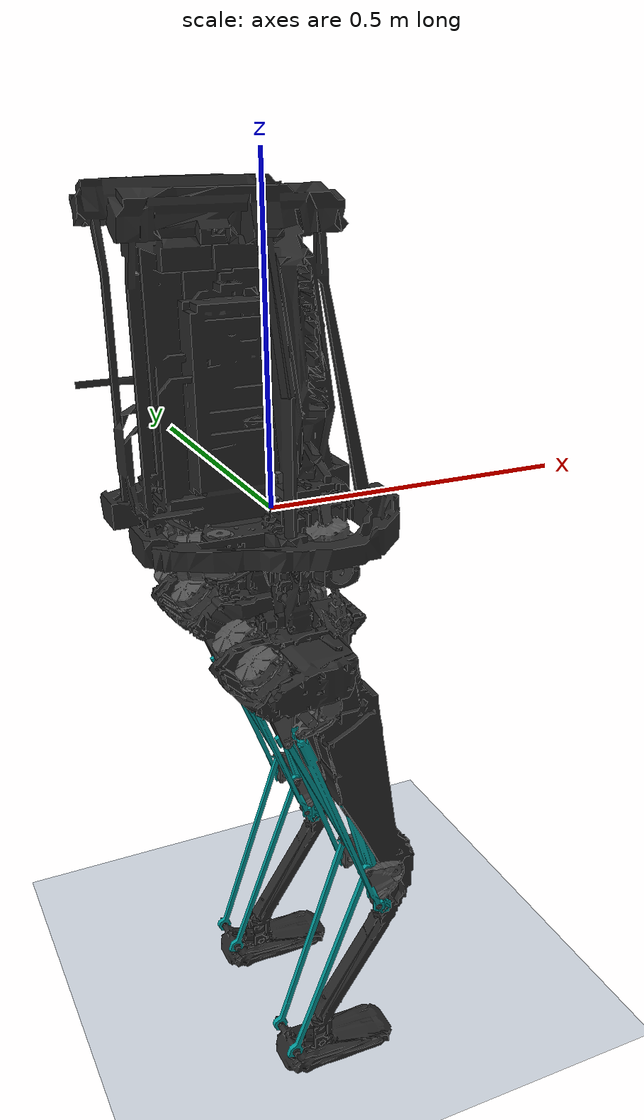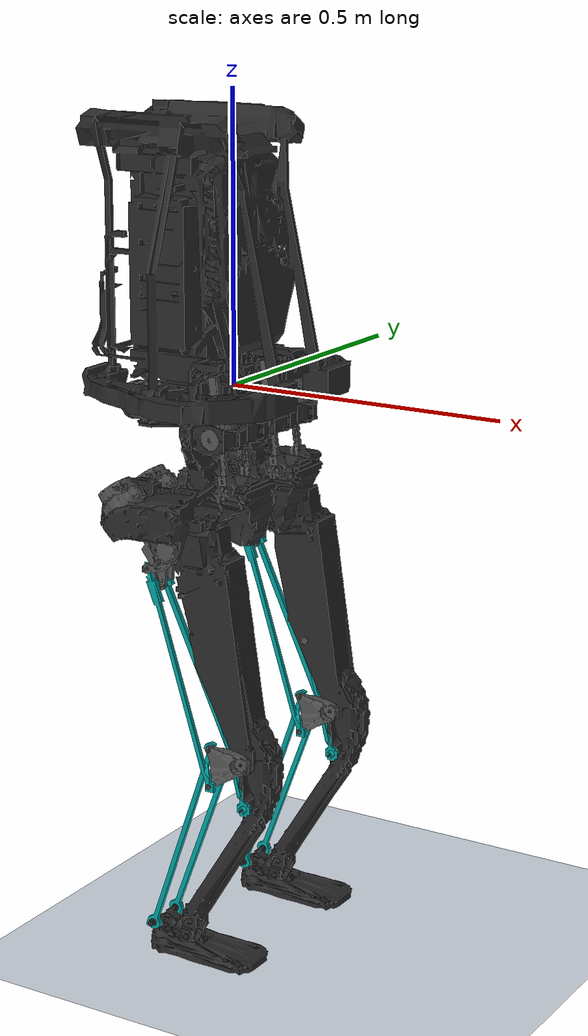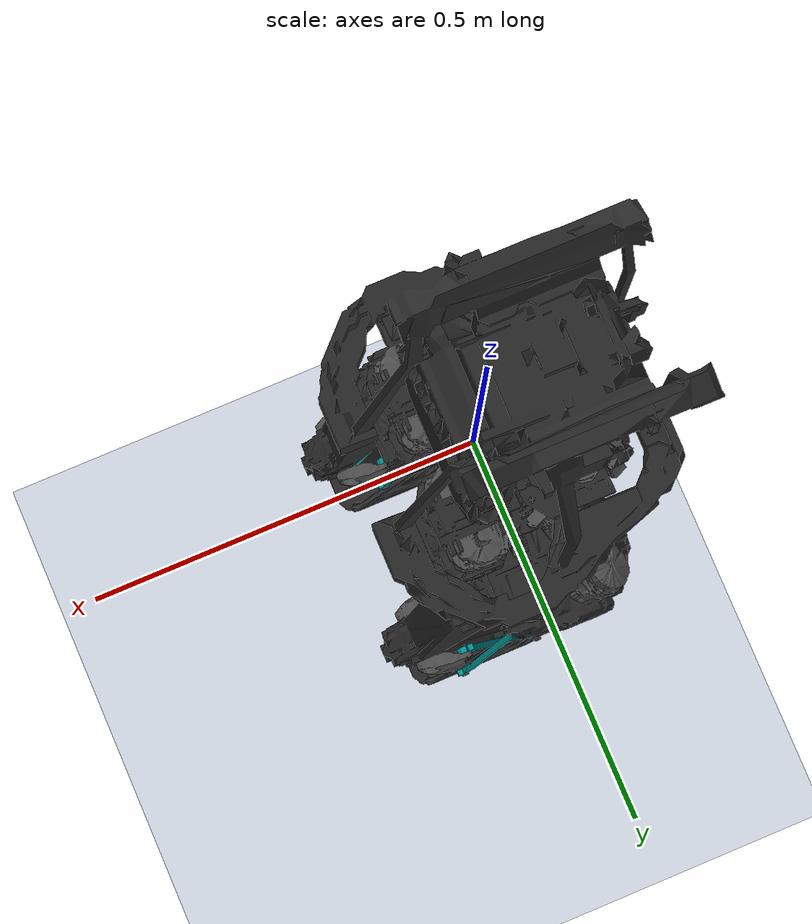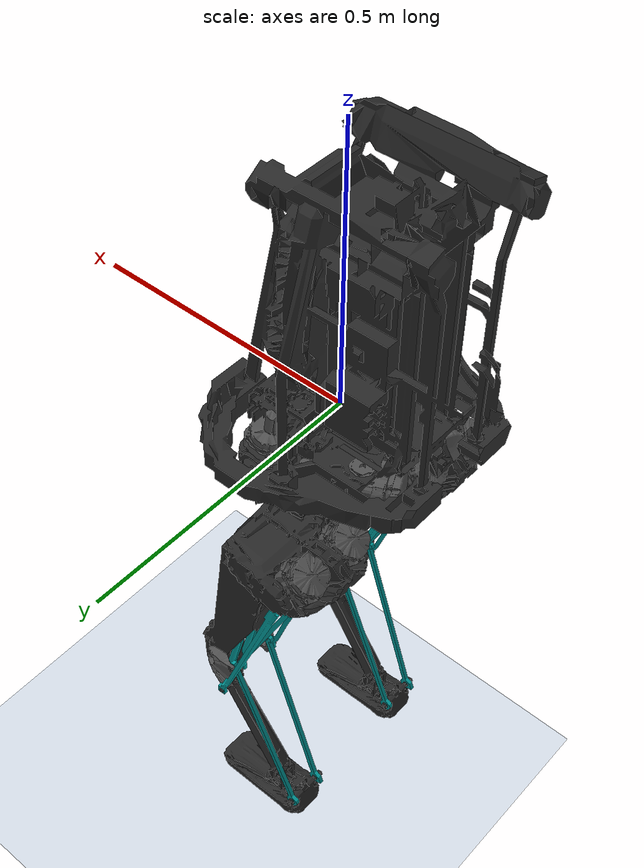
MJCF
<?xml version='1.0' encoding='utf-8'?>
<mujoco model="Kangaroo_published_cut_reconstruction">
  <compiler angle="radian" inertiafromgeom="false" fusestatic="false" meshdir="../upstream/hucebot/kangaroo_mujoco/assets" alignfree="false" />
  <option timestep="5e-05" gravity="0 0 -9.81" integrator="implicitfast" solver="Newton" jacobian="dense" iterations="100" tolerance="1e-12">
    <flag contact="disable" limit="enable" frictionloss="disable" energy="enable" />
  </option>
  <default>
    <geom contype="0" conaffinity="0" />
    <site size=".002" group="5" />
  </default>
  <asset>
    <mesh name="torso" file="Torso.STL" />
    <mesh name="base_link" file="base_link.STL" />
    <mesh name="Yaw_motor" file="Yaw_motor.STL" />
    <mesh name="Hip_yaw" file="Hip_yaw.STL" />
    <mesh name="Yaw_rod" file="Yaw_rod.STL" />
    <mesh name="Hip_roll" file="Hip_roll.STL" />
    <mesh name="Hip_pitch" file="Hip_pitch.STL" />
    <mesh name="Hip_differential_internal_cradle" file="Hip_differential_internal_cradle.STL" />
    <mesh name="Hip_differential_internal_UnivJoint" file="Hip_differential_internal_UnivJoint.STL" />
    <mesh name="Hip_differential_internal_motor" file="Hip_differential_internal_motor.STL" scale="1 -1 1" />
    <mesh name="Hip_differential_internal_rod" file="Hip_differential_internal_rod.STL" scale="1 1 -1" />
    <mesh name="Hip_differential_internal_rod1" file="Hip_differential_internal_rod.STL" scale="-1 1 -1" />
    <mesh name="Yaw_motor1" file="Yaw_motor.STL" scale="1 -1 1" />
    <mesh name="Hip_yaw1" file="Hip_yaw.STL" scale="1 -1 1" />
    <mesh name="Yaw_rod1" file="Yaw_rod.STL" scale="1 1 -1" />
    <mesh name="Hip_roll1" file="Hip_roll.STL" scale="-1 1 1" />
    <mesh name="Hip_pitch1" file="Hip_pitch.STL" scale="-1 1 1" />
    <mesh name="Hip_differential_internal_cradle1" file="Hip_differential_internal_cradle.STL" scale="-1 1 1" />
    <mesh name="Hip_differential_internal_UnivJoint1" file="Hip_differential_internal_UnivJoint.STL" scale="-1 1 1" />
    <mesh name="Hip_differential_internal_cradle2" file="Hip_differential_internal_cradle.STL" scale="1 1 -1" />
    <mesh name="Hip_differential_internal_cradle3" file="Hip_differential_internal_cradle.STL" scale="-1 1 -1" />
    <mesh name="Femour_pitch" file="Femour_pitch.STL" />
    <mesh name="Knee" file="Knee.STL" />
    <mesh name="Femour_pitch1" file="Femour_pitch.STL" scale="1 1 -1" />
    <mesh name="Leg_length_slidinig_nut" file="Leg_length_slidinig_nut.STL" />
    <mesh name="Leg_length_short_bars" file="Leg_length_short_bars.STL" />
    <mesh name="Rear_triangle" file="Rear_triangle.STL" />
    <mesh name="Rear_long_bar" file="Rear_long_bar.STL" />
    <mesh name="Rear_short_bar" file="Rear_short_bar.STL" />
    <mesh name="External_butterfly" file="External_butterfly.STL" />
    <mesh name="External_higher_ankle_bar" file="External_higher_ankle_bar.STL" />
    <mesh name="External_lower_ankle_bar" file="External_lower_ankle_bar.STL" />
    <mesh name="External_butterfly1" file="External_butterfly.STL" scale="1 1 -1" />
    <mesh name="External_higher_ankle_bar1" file="External_higher_ankle_bar.STL" scale="1 1 -1" />
    <mesh name="External_ankle_ball" file="External_ankle_ball.STL" />
    <mesh name="Ankle_roll" file="Ankle_roll.STL" />
    <mesh name="Ankle_pitch" file="Ankle_pitch.STL" />
    <mesh name="External_knee_ball" file="External_knee_ball.STL" />
    <mesh name="Ankle_external_motor" file="Ankle_external_motor.STL" />
    <mesh name="Ankle_external_rod" file="Ankle_external_rod.STL" />
    <mesh name="Ankle_external_pendulum" file="Ankle_external_pendulum.STL" />
    <mesh name="Ankle_external_pendulum1" file="Ankle_external_pendulum.STL" scale="1 1 -1" />
    <mesh name="torso_collision" file="simple/Torso.STL" />
    <mesh name="base_link_collision" file="simple/base_link.STL" />
    <mesh name="Yaw_motor_collision" file="simple/Yaw_motor.STL" />
    <mesh name="Hip_yaw_collision" file="simple/Hip_yaw.STL" />
    <mesh name="Ankle_roll_collision" file="simple/Ankle_roll.STL" />
    <mesh name="Knee_collision" file="simple/Knee.STL" />
    <mesh name="Femour_pitch_collision" file="simple/Femour_pitch.STL" />
    <mesh name="Hip_roll_collision" file="simple/Hip_roll.STL" />
    <mesh name="Hip_roll1_collision" file="simple/Hip_roll.STL" scale="-1 1 1" />
    <mesh name="Hip_differential_internal_cradle_collision" file="simple/Hip_differential_internal_cradle.STL" />
    <mesh name="Hip_differential_internal_cradle2_collision" file="simple/Hip_differential_internal_cradle.STL" scale="-1 1 1" />
    <mesh name="Rear_triangle_collision" file="simple/Rear_triangle.STL" />
    <mesh name="Rear_long_bar_collision" file="simple/Rear_long_bar.STL" />
    <mesh name="External_butterfly_collision" file="simple/External_butterfly.STL" />
    <mesh name="External_butterfly1_collision" file="simple/External_butterfly.STL" scale="1 1 -1" />
    <mesh name="External_higher_ankle_bar_collision" file="simple/External_higher_ankle_bar.STL" />
    <mesh name="External_higher_ankle_bar1_collision" file="simple/External_higher_ankle_bar.STL" scale="1 1 -1" />
    <mesh name="External_lower_ankle_bar_collision" file="simple/External_lower_ankle_bar.STL" />
    <mesh name="Yaw_motor1_collision" file="simple/Yaw_motor.STL" scale="1 -1 1" />
    <mesh name="Hip_yaw1_collision" file="simple/Hip_yaw.STL" scale="1 -1 1" />
    <mesh name="Hip_differential_internal_cradle3_collision" file="simple/Hip_differential_internal_cradle.STL" scale="-1 1 -1" />
    <mesh name="Hip_differential_internal_cradle22_collision" file="simple/Hip_differential_internal_cradle.STL" scale="1 1 -1" />
    <texture type="skybox" builtin="gradient" rgb1=".13 .18 .25" rgb2=".025 .04 .07" width="512" height="3072" />
  </asset>
  <visual>
    <global offwidth="1600" offheight="1000" />
  </visual>
  <worldbody>
    <light pos="1 -2 3" dir="-.3 .5 -1" diffuse=".8 .8 .8" />
    <light pos="-1 2 2" dir=".3 -.5 -1" diffuse=".7 .7 .7" castshadow="false" />
    <geom name="floor" type="plane" size="3 3 .1" pos="0 0 -1.03" rgba=".84 .87 .91 1" contype="0" conaffinity="0" />
    <body name="base_link">
      <inertial mass="1.44985482308619" pos="-0.055595146648293001 8.3634216454369097e-05 -0.028686254999856001" diaginertia="0.0015383577483199643 0.0030913274380091581 0.003984812684888827" quat="0.70780511893659825 0.015345925687140837 0.015267514674370045 0.70607600098546086" />
      <geom rgba="0.15625 0.15625 0.15625 1" mesh="base_link" type="mesh" contype="0" conaffinity="0" group="2" />
      <body name="left_yaw_motor" pos="-0.11139 0.080870999999999998 -0.029499999999999998" quat="0.83867509600775636 0 0 -0.54463206234703121">
        <inertial mass="0.69585" pos="-4.1275900000000002e-05 -0.016478599999999999 -0.00015095000000000001" diaginertia="0.00019140499999999993 0.00020741099999999993 0.00029985199999999987" quat="-0.70632066135802429 0.70754041965032977 -0.010876001329825033 -0.019477948939039261" />
        <geom rgba="0.3125 0.3125 0.3125 1" mesh="Yaw_motor" type="mesh" contype="0" conaffinity="0" group="2" />
        <joint name="left_yaw_motor_joint" type="hinge" axis="0 0 -1" limited="true" range="-3.1415899999999999 3.1415899999999999" armature="0.0" damping="3.0" frictionloss="0" />
        <body name="left_yaw_rod" pos="0 0.0877 0" quat="-2.5973410328296309e-06 -2.5973510328336068e-06 0.70710828118078273 0.70710528117958982">
          <inertial mass="0.124518" pos="4.2229299999999999e-05 1.30303e-05 -0.047761900000000003" diaginertia="5.5451700000000037e-06 6.3391499999999957e-05 6.6245600000000001e-05" quat="0.70732903783469914 1.5298805995419276e-05 -0.7068844543675824 -1.3237476693245352e-05" />
          <geom rgba="0.3125 0.3125 0.3125 1" mesh="Yaw_rod" type="mesh" contype="0" conaffinity="0" group="2" />
          <joint name="leg_left_1_motor" type="slide" axis="9.4797658307788301e-18 -4.2426423741001299e-06 -0.99999999999100009" limited="true" range="-0.02 0.02" armature="0.01" damping="3.0" frictionloss="0" />
          <site name="left_hip_yaw_closed_a" pos="0 0 0" />
        </body>
      </body>
      <body name="left_hip_yaw" pos="-0.014999999999999999 0.080000000000000002 -0.058500000000000003" quat="-0.70710528118436011 0 0 0.70710828118555302">
        <inertial mass="0.867837" pos="0.0025800300000000001 0.018407099999999999 -0.00083598199999999998" diaginertia="0.00056635900000000033 0.00094694000000000061 0.0010785100000000004" quat="0.49942598615641187 0.52755524776991958 0.51843824103079938 -0.45108861118299681" />
        <geom rgba="0.15625 0.15625 0.15625 1" mesh="Hip_yaw" type="mesh" contype="0" conaffinity="0" group="2" />
        <joint name="leg_left_1_joint" type="hinge" axis="0 0 -1" limited="true" range="-0.78539800000000004 0.261799" armature="0.0" damping="3.0" frictionloss="0" />
        <body name="left_hip_differential_2_cradle" pos="-0.035000000000000003 0.0625 0.00014999999999999999" quat="-2.5973410328296309e-06 -2.5973510328336068e-06 0.70710828118078273 0.70710528117958982">
          <inertial mass="0.138052" pos="-0.0013821599999999999 2.1695499999999998e-06 -0.0105801" diaginertia="2.9932400000000022e-05 0.00011860100000000001 0.000122729" quat="0.63736902802779738 -4.1551655383103415e-05 0.77055870443318164 5.8366234547996236e-05" />
          <geom rgba="0.15625 0.15625 0.15625 1" mesh="Hip_differential_internal_cradle1" type="mesh" contype="0" conaffinity="0" group="2" />
          <joint name="left_hip_differential_2_cradle_joint" type="hinge" axis="0 0 -1" limited="true" range="-3.1415899999999999 3.1415899999999999" armature="0.0" damping="3.0" frictionloss="0" />
          <body name="left_hip_differential_2_motor" pos="0 0 0" quat="-2.5973410328296309e-06 0.70710528117958982 2.5973510328336068e-06 0.70710828118078273">
            <inertial mass="0.698684" pos="-0.0022017999999999999 0.016612399999999999 -0.00015337400000000001" diaginertia="0.00019332000000000011 0.00020931199999999999 0.00030039600000000019" quat="0.7036411032991321 0.70642003236645645 0.035940108830764581 0.067588787506416323" />
            <geom rgba="0.3125 0.3125 0.3125 1" mesh="Hip_differential_internal_motor" type="mesh" contype="0" conaffinity="0" group="2" />
            <joint name="left_hip_differential_2_motor_joint" type="hinge" axis="0 0 -1" limited="true" range="-3.1415899999999999 3.1415899999999999" armature="0.0" damping="3.0" frictionloss="0" />
            <body name="left_hip_differential_2_rod" pos="0.012500000000000001 0.092649999999999996 0" quat="-0.46537517398961614 0.53237619903926059 0.46537617398999004 0.53237819904000827">
              <inertial mass="0.142095" pos="0.00068910200000000003 5.2800100000000003e-05 -0.0626747" diaginertia="4.8995599999999579e-06 0.00013658899999999998 0.00013778900000000011" quat="0.50012316270583923 0.50004193186836621 0.50022179727241556 -0.49961289217955079" />
              <geom rgba="0.3125 0.3125 0.3125 1" mesh="Hip_differential_internal_rod" type="mesh" contype="0" conaffinity="0" group="2" />
              <joint name="leg_left_2_motor" type="slide" axis="0 0 -1" limited="true" range="-0.040000000000000001 0.040000000000000001" armature="0.01" damping="3.0" frictionloss="0" />
              <site name="left_hip_differential_2a_b" pos="-7.1939563315423431e-07 1.1344003292336118e-06 -5.4704819382910734e-06" />
              <site name="left_hip_differential_2a_ub" pos="8.2961344347951533e-07 0.013362517368230537 -0.09910881776539622" />
            </body>
          </body>
        </body>
        <body name="left_hip_differential_3_cradle" pos="0.035000000000000003 0.0625 0.00014999999999999999" quat="-2.5973410328296309e-06 -2.5973510328336068e-06 0.70710828118078273 0.70710528117958982">
          <inertial mass="0.138052" pos="-0.0013821599999999999 2.1695499999999998e-06 -0.0105801" diaginertia="2.9932400000000022e-05 0.00011860100000000001 0.000122729" quat="-4.1551655383103415e-05 0.63736902802779749 5.8366234547996242e-05 0.77055870443318175" />
          <geom rgba="0.15625 0.15625 0.15625 1" mesh="Hip_differential_internal_cradle" type="mesh" contype="0" conaffinity="0" group="2" />
          <joint name="left_hip_differential_3_cradle_joint" type="hinge" axis="0 0 -1" limited="true" range="-3.1415899999999999 3.1415899999999999" armature="0.0" damping="3.0" frictionloss="0" />
          <body name="left_hip_differential_3_motor" pos="0 0 0" quat="-2.5973410328296309e-06 0.70710528117958982 2.5973510328336068e-06 0.70710828118078273">
            <inertial mass="0.698684" pos="-0.0022017999999999999 0.016612399999999999 -0.00015337400000000001" diaginertia="0.00019332000000000011 0.00020931199999999999 0.00030039600000000019" quat="0.7036411032991321 0.70642003236645645 0.035940108830764581 0.067588787506416323" />
            <geom rgba="0.3125 0.3125 0.3125 1" mesh="Hip_differential_internal_motor" type="mesh" contype="0" conaffinity="0" group="2" />
            <joint name="left_hip_differential_3_motor_joint" type="hinge" axis="0 0 -1" limited="true" range="-3.1415899999999999 3.1415899999999999" armature="0.0" damping="3.0" frictionloss="0" />
            <body name="left_hip_differential_3_rod" pos="0.012500000000000001 0.092649999999999996 0" quat="-0.46537517398961614 0.53237619903926059 0.46537617398999004 0.53237819904000827">
              <inertial mass="0.142095" pos="0.00068910200000000003 5.2800100000000003e-05 -0.0626747" diaginertia="4.8995599999999579e-06 0.00013658899999999998 0.00013778900000000011" quat="0.50012316270583923 0.50004193186836621 0.50022179727241556 -0.49961289217955079" />
              <geom rgba="0.3125 0.3125 0.3125 1" mesh="Hip_differential_internal_rod1" type="mesh" contype="0" conaffinity="0" group="2" />
              <joint name="leg_left_3_motor" type="slide" axis="0 0 -1" limited="true" range="-0.040000000000000001 0.040000000000000001" armature="0.01" damping="3.0" frictionloss="0" />
              <site name="left_hip_differential_3a_b" pos="-7.1939563315423431e-07 1.1344003292404882e-06 -5.4704819382901459e-06" />
              <site name="left_hip_differential_3a_ub" pos="8.2961344347951533e-07 0.013362517368230544 -0.09910881776539622" />
            </body>
          </body>
        </body>
        <body name="left_hip_pitch" pos="0 0.014999999999999999 -0.092499999999999999" quat="0.50002299947097573 -0.49997699947102436 0.50002299947097573 -0.49997699947102436">
          <inertial mass="0.0907288" pos="-0.00299643 6.76272e-10 0.00010129299999999999" diaginertia="6.1039799999999998e-06 3.6423799999999995e-05 3.9047099999999987e-05" quat="1.3045122428022769e-15 0.99999985521966628 -8.0933705286416979e-19 0.00053810839655848942" />
          <geom rgba="0.15625 0.15625 0.15625 1" mesh="Hip_pitch" type="mesh" contype="0" conaffinity="0" group="2" />
          <joint name="leg_left_2_joint" type="hinge" axis="0 0 -1" limited="true" range="-0.74174300000000004 0.74174300000000004" armature="0.0" damping="3.0" frictionloss="0" />
          <body name="left_hip_roll" pos="0 0 0" quat="0 0.70710678118654746 0 0.70710678118654768">
            <inertial mass="2.07276" pos="-0.034265999999999998 -0.039022000000000001 0.0098612000000000005" diaginertia="0.0018172599999999994 0.00292998 0.0031733700000000009" quat="-0.65379263524154074 -0.018515210526319471 0.75595864382643863 0.027182823752867038" />
            <geom rgba="0.15625 0.15625 0.15625 1" mesh="Hip_roll" type="mesh" contype="0" conaffinity="0" group="2" />
            <joint name="leg_left_3_joint" type="hinge" axis="0 0 -1" limited="true" range="-0.471225 0.471225" armature="0.0" damping="3.0" frictionloss="0" />
            <body name="left_ankle_4_motor" pos="-0.019 -0.046649999999999997 0.075084399999999996" quat="-0.70710678118654768 0 0.70710678118654746 0">
              <inertial mass="0.69585" pos="0.0097648600000000002 0.0132739 -0.00015095000000000001" diaginertia="0.00019140499999999999 0.00020741100000000009 0.00029985199999999987" quat="0.67742664164821242 0.66915632121774649 -0.23013354537094444 -0.20090175274137337" />
              <geom rgba="0.3125 0.3125 0.3125 1" mesh="Ankle_external_motor" type="mesh" contype="0" conaffinity="0" group="2" />
              <joint name="left_ankle_4_motor_joint" type="hinge" axis="0 0 1" limited="true" range="-3.1415899999999999 3.1415899999999999" armature="0.0" damping="3.0" frictionloss="0" />
              <body name="left_ankle_4_rod" pos="-0.0464141 -0.063425200000000001 0" quat="-0.6305862099114643 -0.31993910650230728 0.6305862099114643 -0.31993910650230728">
                <inertial mass="0.124518" pos="-1.30338e-05 4.2228200000000003e-05 -0.047761900000000003" diaginertia="5.5451700000000122e-06 6.3391699999999985e-05 6.6245800000000002e-05" quat="-0.4998542935545558 0.50016590833005803 0.5001484852252257 0.49983121359750621" />
                <geom rgba="0.3125 0.3125 0.3125 1" mesh="Ankle_external_rod" type="mesh" contype="0" conaffinity="0" group="2" />
                <joint name="leg_left_4_motor" type="slide" axis="0 0 -1" limited="true" range="-0.02 0.02" armature="0.01" damping="3.0" frictionloss="0" />
                <site name="left_ankle_hip_4_closed_a" pos="0 0 0" />
              </body>
            </body>
            <body name="left_ankle_4_pendulum" pos="-0.019 -0.089999999999999997 0" quat="-0.70710678118654768 0 0.70710678118654746 0">
              <inertial mass="0.0647795" pos="0.015271 -0.016307599999999998 -0.0074903900000000004" diaginertia="7.1926400000000091e-06 2.1437800000000014e-05 2.4818800000000014e-05" quat="0.94798651310325699 -0.053687097730113022 -0.05919546113238619 -0.30811550414247213" />
              <geom rgba="0.3125 0.3125 0.3125 1" mesh="Ankle_external_pendulum1" type="mesh" contype="0" conaffinity="0" group="2" />
              <joint name="left_ankle_4_pendulum_joint" type="hinge" axis="0 0 -1" limited="true" range="-3.1415899999999999 3.1415899999999999" armature="0.0" damping="3.0" frictionloss="0" />
              <body name="left_4_higher_ankle_bar" pos="0.045962700000000002 -0.038567299999999999 0" quat="0 0 1 0">
                <inertial mass="0.108309" pos="0.063571100000000005 -0.17466000000000001 0.0088043500000000007" diaginertia="1.6186600000000932e-06 0.00063397700000000009 0.00063431799999999993" quat="0.81892289819951902 -0.013573620238286324 -0.019384623109682916 -0.57341545150529594" />
                <geom rgba="0 0.597656 0.597656 1" mesh="External_higher_ankle_bar1" type="mesh" contype="0" conaffinity="0" group="2" />
                <joint name="left_4_higher_ankle_bar_joint" type="hinge" axis="0 0 -1" limited="true" range="-3.1415899999999999 3.1415899999999999" armature="0.0" damping="3.0" frictionloss="0" />
                <site name="left_butterfly_4_closed_b" pos="0.12996770000000016 -0.35708270000000036 0.025100000000000018" />
              </body>
              <site name="left_ankle_hip_4_closed_b" pos="0.028670300000000027 -0.020075200000000015 1.017080797496046e-17" />
            </body>
            <body name="left_ankle_5_motor" pos="-0.115 -0.046649999999999997 0.075084399999999996" quat="-0.70710678118654768 0 0.70710678118654746 0">
              <inertial mass="0.69585" pos="0.0097648600000000002 0.0132739 -0.00015095000000000001" diaginertia="0.00019140499999999999 0.00020741100000000009 0.00029985199999999987" quat="0.67742664164821242 0.66915632121774649 -0.23013354537094444 -0.20090175274137337" />
              <geom rgba="0.3125 0.3125 0.3125 1" mesh="Ankle_external_motor" type="mesh" contype="0" conaffinity="0" group="2" />
              <joint name="left_ankle_5_motor_joint" type="hinge" axis="0 0 1" limited="true" range="-3.1415899999999999 3.1415899999999999" armature="0.0" damping="3.0" frictionloss="0" />
              <body name="left_ankle_5_rod" pos="-0.0464141 -0.063425200000000001 0" quat="-0.6305862099114643 -0.31993910650230728 0.6305862099114643 -0.31993910650230728">
                <inertial mass="0.124518" pos="-1.30338e-05 4.2228200000000003e-05 -0.047761900000000003" diaginertia="5.5451700000000122e-06 6.3391699999999985e-05 6.6245800000000002e-05" quat="-0.4998542935545558 0.50016590833005803 0.5001484852252257 0.49983121359750621" />
                <geom rgba="0.3125 0.3125 0.3125 1" mesh="Ankle_external_rod" type="mesh" contype="0" conaffinity="0" group="2" />
                <joint name="leg_left_5_motor" type="slide" axis="0 0 -1" limited="true" range="-0.02 0.02" armature="0.01" damping="3.0" frictionloss="0" />
                <site name="left_ankle_hip_5_closed_a" pos="0 0 0" />
              </body>
            </body>
            <body name="left_ankle_5_pendulum" pos="-0.115 -0.089999999999999997 0" quat="-0.70710678118654768 0 0.70710678118654746 0">
              <inertial mass="0.0647795" pos="0.015271 -0.016307599999999998 0.0074903900000000004" diaginertia="7.1926400000000032e-06 2.143780000000001e-05 2.4818800000000014e-05" quat="0.94798651310325688 0.053687097730113105 0.059195461132386148 -0.30811550414247235" />
              <geom rgba="0.3125 0.3125 0.3125 1" mesh="Ankle_external_pendulum" type="mesh" contype="0" conaffinity="0" group="2" />
              <joint name="left_ankle_5_pendulum_joint" type="hinge" axis="0 0 -1" limited="true" range="-3.1415899999999999 3.1415899999999999" armature="0.0" damping="3.0" frictionloss="0" />
              <body name="left_5_higher_ankle_bar" pos="0.045962700000000002 -0.038567299999999999 0" quat="0 0 1 0">
                <inertial mass="0.108309" pos="0.063571100000000005 -0.17466000000000001 -0.0088043500000000007" diaginertia="1.6186599999999877e-06 0.00063397700000000009 0.00063431799999999982" quat="-0.019384623109683093 0.57341545150529583 0.81892289819951924 0.013573620238286073" />
                <geom rgba="0 0.597656 0.597656 1" mesh="External_higher_ankle_bar" type="mesh" contype="0" conaffinity="0" group="2" />
                <joint name="left_5_higher_ankle_bar_joint" type="hinge" axis="0 0 -1" limited="true" range="-3.1415899999999999 3.1415899999999999" armature="0.0" damping="3.0" frictionloss="0" />
                <site name="left_butterfly_5_closed_b" pos="0.12996770000000019 -0.35708270000000036 -0.024900000000000054" />
              </body>
              <site name="left_ankle_hip_5_closed_b" pos="0.028670300000000017 -0.020075200000000015 2.4048622252429627e-17" />
            </body>
            <body name="left_hip_differential_2_univ" pos="-0.035000000000000003 0 -0.059999999999999998" quat="1.3492399999817955e-11 -3.6732099999504398e-06 0.99999999998650757 -3.6732099999504398e-06">
              <inertial mass="0.0543984" pos="0.00057667299999999999 -0.00056915600000000002 0.00088379500000000004" diaginertia="1.745620000000001e-06 8.1241700000000039e-06 8.6648000000000038e-06" quat="0.49868293707394085 0.50132341523045643 -0.4994192358582667 0.50057026326753018" />
              <geom rgba="0.3125 0.3125 0.3125 1" mesh="Hip_differential_internal_UnivJoint1" type="mesh" contype="0" conaffinity="0" group="2" />
              <joint name="left_hip_differential_2_univ_joint" type="hinge" axis="0 0 -1" limited="true" range="-3.1415899999999999 3.1415899999999999" armature="0.0" damping="3.0" frictionloss="0" />
              <site name="left_hip_differential_2a_a" pos="0 0 0" />
              <site name="left_hip_differential_2a_ua" pos="0.10000000000000001 0 0" />
            </body>
            <body name="left_hip_differential_3_univ" pos="0.035000000000000003 0 -0.059999999999999998" quat="1.3492399999817955e-11 -3.6732099999504398e-06 0.99999999998650757 -3.6732099999504398e-06">
              <inertial mass="0.0543984" pos="0.00057667299999999999 -0.00056915600000000002 0.00088379500000000004" diaginertia="1.745620000000001e-06 8.1241700000000056e-06 8.6648000000000055e-06" quat="-0.50057026326752962 -0.49941923585826703 0.50132341523045598 -0.49868293707394129" />
              <geom rgba="0.3125 0.3125 0.3125 1" mesh="Hip_differential_internal_UnivJoint" type="mesh" contype="0" conaffinity="0" group="2" />
              <joint name="left_hip_differential_3_univ_joint" type="hinge" axis="0 0 -1" limited="true" range="-3.1415899999999999 3.1415899999999999" armature="0.0" damping="3.0" frictionloss="0" />
              <site name="left_hip_differential_3a_a" pos="0 0 0" />
              <site name="left_hip_differential_3a_ua" pos="0.10000000000000001 0 0" />
            </body>
            <body name="left_rear_short_bar" pos="-0.066900000000000001 -0.017628000000000001 0.089371999999999993" quat="0.70263300976976784 0.07941570110423643 0.70263300976976772 0.07941570110423643">
              <inertial mass="0.0877852" pos="1.8785400000000001e-07 -0.045020900000000003 -2.8002300000000002e-07" diaginertia="2.8649099999999972e-06 1.4874600000000002e-05 1.6544499999999997e-05" quat="0.70710748827565095 4.949747468264348e-06 4.9497474683580045e-06 0.7071060740620887" />
              <geom rgba="0 0.597656 0.597656 1" mesh="Rear_short_bar" type="mesh" contype="0" conaffinity="0" group="2" />
              <joint name="left_rear_short_bar_joint" type="hinge" axis="0 0 -1" limited="true" range="-3.1415899999999999 3.1415899999999999" armature="0.0" damping="3.0" frictionloss="0" />
              <body name="left_rear_triangle" pos="0 -0.089999999999999997 0" quat="1 0 0 0">
                <inertial mass="0.107984" pos="0.0142194 -0.019473799999999999 0.00024432799999999998" diaginertia="1.2939500000000011e-05 5.7461600000000019e-05 6.5565099999999993e-05" quat="-0.62890088184212078 -0.0029493429032646746 0.001937472921348679 0.77747747774023712" />
                <geom rgba="0.3125 0.3125 0.3125 1" mesh="Rear_triangle" type="mesh" contype="0" conaffinity="0" group="2" />
                <joint name="left_rear_triangle_joint" type="hinge" axis="0 0 1" limited="true" range="-3.1415899999999999 3.1415899999999999" armature="0.0" damping="3.0" frictionloss="0" />
                <body name="left_rear_long_bar" pos="0.0079431999999999992 -0.067421999999999996 0" quat="0.99474793557564933 0 0 0.10235499337103024">
                  <inertial mass="0.16896" pos="8.9974299999999999e-08 -0.20219200000000001 -1.2441199999999999e-07" diaginertia="4.8936099999999999e-06 0.00099094099999999996 0.00099261100000000001" quat="-0.70710678118654746 0 0 0.70710678118654746" />
                  <geom rgba="0 0.597656 0.597656 1" mesh="Rear_long_bar" type="mesh" contype="0" conaffinity="0" group="2" />
                  <joint name="left_rear_long_bar_joint" type="hinge" axis="0 0 -1" limited="true" range="-3.1415899999999999 3.1415899999999999" armature="0.0" damping="3.0" frictionloss="0" />
                  <site name="left_rear_triangle_closed_2_a" pos="0 -0.40427000000000002 0" />
                </body>
                <site name="left_rear_triangle_closed_1_b" pos="0.035612423240737198 0.018221508117524519 -3.577845156864249e-19" />
              </body>
            </body>
            <body name="left_femour_pitch" pos="-0.066900000000000001 -0.089999999999999997 0" quat="0.70710678118654768 0 0.70710678118654746 0">
              <inertial mass="2.17531" pos="0.058175600000000001 -0.098513400000000001 -0.00023561099999999999" diaginertia="0.0016044800000000036 0.0096015000000000024 0.0098234500000000009" quat="0.78982636138828666 0.030709651691290044 -0.025691314181433299 -0.61202221571179116" />
              <geom rgba="0.15625 0.15625 0.15625 1" mesh="Femour_pitch" type="mesh" contype="0" conaffinity="0" group="2" />
              <joint name="leg_left_femour_joint" type="hinge" axis="0 0 -1" limited="true" range="-3.1415899999999999 3.1415899999999999" armature="0.0" damping="3.0" frictionloss="0" />
              <body name="left_knee" pos="0.129968 -0.35708299999999998 0" quat="1 0 0 0">
                <inertial mass="0.621373" pos="-0.021264600000000002 -0.11802799999999999 0.000114812" diaginertia="0.00022992099999999998 0.0011366900000000005 0.0012048900000000008" quat="-0.62445762059996646 0.0013159263697369035 -0.0022740565314743558 0.78105427281291384" />
                <geom rgba="0.15625 0.15625 0.15625 1" mesh="Knee" type="mesh" contype="0" conaffinity="0" group="2" />
                <joint name="leg_left_knee_joint" type="hinge" axis="0 0 -1" limited="true" range="0 3.1415899999999999" armature="0.0" damping="3.0" frictionloss="0" />
                <body name="left_4_butterfly" pos="0 0 0.042999999999999997" quat="1 0 0 0">
                  <inertial mass="0.082315" pos="-0.024871600000000001 -0.00598892 0.0050616699999999999" diaginertia="2.0985400000000028e-05 2.4980900000000014e-05 4.2339500000000003e-05" quat="-0.012036379900128794 0.81259423628302796 0.57025514081879414 -0.11981154822570132" />
                  <geom rgba="0.3125 0.3125 0.3125 1" mesh="External_butterfly1" type="mesh" contype="0" conaffinity="0" group="2" />
                  <joint name="left_4_butterfly_joint" type="hinge" axis="0 0 -1" limited="true" range="-3.1415899999999999 3.1415899999999999" armature="0.0" damping="3.0" frictionloss="0" />
                  <body name="left_4_knee_ball" pos="-0.056381000000000001 0.020521000000000001 -0.00050000000000000001" quat="-1.3492399999817955e-11 -3.6732099999504398e-06 0.99999999998650757 3.6732099999504398e-06">
                    <inertial mass="0.00195231" pos="3.4080899999999999e-12 -8.7998500000000003e-12 0" diaginertia="3.17847e-08 3.17847e-08 4.3005300000000003e-08" quat="1 0 0 0" />
                    <geom rgba="0.15625 0.15625 0.15625 1" mesh="External_knee_ball" type="mesh" contype="0" conaffinity="0" group="2" />
                    <joint name="left_4_knee_ball_joint" type="hinge" axis="0 0 -1" limited="true" range="-3.1415899999999999 3.1415899999999999" armature="0.0" damping="3.0" frictionloss="0" />
                    <body name="left_4_lower_ankle_bar" pos="0 0 0" quat="-0.69635883143766075 -0.12280997027231516 0.69636183143693464 -0.12280997027231516">
                      <inertial mass="0.125467" pos="0.0043189400000000003 -0.218831 -6.75122e-08" diaginertia="2.48422e-06 0.00060771199999999984 0.00060871799999999985" quat="0.50490930765244157 0.50490930765244157 -0.4950420093748934 -0.4950420093748934" />
                      <geom rgba="0 0.597656 0.597656 1" mesh="External_lower_ankle_bar" type="mesh" contype="0" conaffinity="0" group="2" />
                      <joint name="left_4_lower_ankle_bar_joint" type="hinge" axis="0 0 -1" limited="true" range="-3.1415899999999999 3.1415899999999999" armature="0.0" damping="3.0" frictionloss="0" />
                      <site name="left_ankle_4_closed_a" pos="0.0074999999999999997 -0.38 0" />
                      <site name="left_ankle_4_closed_ua" pos="0.009474054561576864 -0.28001949209279414 3.3870416020026519e-05" />
                    </body>
                  </body>
                  <site name="left_butterfly_4_closed_a" pos="-0.045962999999999997 -0.038566999999999997 0.029999999999999999" />
                </body>
                <body name="left_5_butterfly" pos="0 0 -0.042999999999999997" quat="1 0 0 0">
                  <inertial mass="0.082315" pos="-0.024871600000000001 -0.00598892 -0.0050616699999999999" diaginertia="2.0985400000000007e-05 2.4980900000000003e-05 4.233950000000001e-05" quat="-0.5702551408187948 -0.11981154822570143 0.012036379900128446 0.81259423628302752" />
                  <geom rgba="0.3125 0.3125 0.3125 1" mesh="External_butterfly" type="mesh" contype="0" conaffinity="0" group="2" />
                  <joint name="left_5_butterfly_joint" type="hinge" axis="0 0 -1" limited="true" range="-3.1415899999999999 3.1415899999999999" armature="0.0" damping="3.0" frictionloss="0" />
                  <body name="left_5_knee_ball" pos="-0.056381000000000001 0.020521000000000001 0.00050000000000000001" quat="-1.3492399999817955e-11 -3.6732099999504398e-06 0.99999999998650757 3.6732099999504398e-06">
                    <inertial mass="0.00195231" pos="3.4080899999999999e-12 -8.7998500000000003e-12 0" diaginertia="3.17847e-08 3.17847e-08 4.3005300000000003e-08" quat="1 0 0 0" />
                    <joint name="left_5_knee_ball_joint" type="hinge" axis="0 0 -1" limited="true" range="-3.1415899999999999 3.1415899999999999" armature="0.0" damping="3.0" frictionloss="0" />
                    <body name="left_5_lower_ankle_bar" pos="0 0 0" quat="0.69635883143766075 -0.12280997027231516 0.69636183143693464 0.12280997027231516">
                      <inertial mass="0.125467" pos="0.0043189400000000003 -0.218831 -6.75122e-08" diaginertia="2.48422e-06 0.00060771199999999984 0.00060871799999999985" quat="0.50490930765244157 0.50490930765244157 -0.4950420093748934 -0.4950420093748934" />
                      <geom rgba="0 0.597656 0.597656 1" mesh="External_lower_ankle_bar" type="mesh" contype="0" conaffinity="0" group="2" />
                      <joint name="left_5_lower_ankle_bar_joint" type="hinge" axis="0 0 -1" limited="true" range="-3.1415899999999999 3.1415899999999999" armature="0.0" damping="3.0" frictionloss="0" />
                      <site name="left_ankle_5_closed_a" pos="0.0074999999999999997 -0.38 0" />
                      <site name="left_ankle_5_closed_ua" pos="0.0094739071121282634 -0.47998051619892529 -8.4444745268981636e-06" />
                    </body>
                  </body>
                  <site name="left_butterfly_5_closed_a" pos="-0.045962999999999997 -0.038566999999999997 -0.029999999999999999" />
                </body>
                <body name="left_ankle_pitch" pos="-0.12998899999999999 -0.35707499999999998 0" quat="0.98480779084260428 0 0 -0.17364796311995492">
                  <inertial mass="0.0905838" pos="-0.0075999500000000003 5.8828100000000001e-08 6.9499699999999997e-09" diaginertia="4.0526400000000002e-06 2.9276299999999989e-05 2.9886299999999995e-05" quat="-0.70710324564344873 0.70711031671126146 -7.0710678111840399e-07 7.071067811898275e-07" />
                  <geom rgba="0.15625 0.15625 0.15625 1" mesh="Ankle_pitch" type="mesh" contype="0" conaffinity="0" group="2" />
                  <joint name="leg_left_4_joint" type="hinge" axis="0 0 1" limited="true" range="-0.74174300000000004 0.74174300000000004" armature="0.0" damping="3.0" frictionloss="0" />
                  <body name="left_ankle_roll" pos="0 0 0" quat="0.70710528118436011 0 0.70710828118555302 0">
                    <inertial mass="0.413448" pos="-3.9165200000000002e-05 -0.0099052500000000009 0.022055000000000002" diaginertia="0.00025856200000000037 0.0011707800000000002 0.0013810400000000005" quat="-0.41657982977258273 0.57135768529772002 0.57137960560217227 0.4165777084527969" />
                    <geom rgba="0.15625 0.15625 0.15625 1" mesh="Ankle_roll" type="mesh" contype="0" conaffinity="0" group="2" />
                    <joint name="leg_left_5_joint" type="hinge" axis="0 0 -1" limited="true" range="-0.471225 0.471225" armature="0.0" damping="3.0" frictionloss="0" />
                    <body name="left_4_ankle_ball" pos="-0.035000000000000003 0 -0.059999999999999998" quat="0.70710678036640406 3.4056689421692214e-05 0.70710678036640406 3.4056689421692214e-05">
                      <inertial mass="0.00381364" pos="1.3379499999999999e-07 -9.5634700000000006e-08 -8.4980099999999993e-09" diaginertia="1.01443e-07 1.01443e-07 1.35766e-07" quat="1 0 0 0" />
                      <geom rgba="0.15625 0.15625 0.15625 1" mesh="External_ankle_ball" type="mesh" contype="0" conaffinity="0" group="2" />
                      <joint name="left_4_ankle_ball_joint" type="hinge" axis="0 0.019732905669586159 -0.99980528726039208" limited="true" range="-3.1415899999999999 3.1415899999999999" armature="0.0" damping="3.0" frictionloss="0" />
                      <site name="left_ankle_4_closed_b" pos="-1.9200786866831965e-06 -3.22211392989008e-07 3.1577788579234564e-06" />
                      <site name="left_ankle_4_closed_ub" pos="0.099998075443664555 2.9597364964140599e-05 3.7482940166771275e-06" />
                    </body>
                    <body name="left_5_ankle_ball" pos="0.035000000000000003 0 -0.059999999999999998" quat="0.70710678036640406 3.4056689421692214e-05 0.70710678036640406 3.4056689421692214e-05">
                      <inertial mass="0.00381364" pos="1.3379499999999999e-07 -9.5634700000000006e-08 -8.4980099999999993e-09" diaginertia="1.01443e-07 1.01443e-07 1.35766e-07" quat="1 0 0 0" />
                      <geom rgba="0.15625 0.15625 0.15625 1" mesh="External_ankle_ball" type="mesh" contype="0" conaffinity="0" group="2" />
                      <joint name="left_5_ankle_ball_joint" type="hinge" axis="0 0.019732905669586159 -0.99980528726039208" limited="true" range="-3.1415899999999999 3.1415899999999999" armature="0.0" damping="3.0" frictionloss="0" />
                      <site name="left_ankle_5_closed_b" pos="-2.2547627275027992e-06 -4.2573340991951257e-07 2.5977652788016781e-06" />
                      <site name="left_ankle_5_closed_ub" pos="-0.1000022539931856 1.1977833718577497e-05 2.8425713657785727e-06" />
                    </body>
                  </body>
                </body>
                <site name="left_knee_closed_a" pos="-0.0078440000000000003 -0.089658000000000002 0" />
                <site name="left_rear_triangle_closed_2_b" pos="-0.007871339936427019 -0.089662400656603164 -2.1273173674008163e-17" />
              </body>
              <body name="left_leg_length_slidinig_nut" pos="0.068661399999999997 -0.23849400000000001 0" quat="0.53768818292961629 0.45922915623667393 0.53768818292961629 -0.45922915623667393">
                <inertial mass="0.5431" pos="0.00025698499999999999 0.0014713899999999999 -0.033478599999999997" diaginertia="0.00011244099999999999 0.00016609699999999998 0.00017354399999999984" quat="-0.50855347787291427 0.48431066108725185 0.53639257116516414 0.468080712377061" />
                <geom rgba="0.3125 0.3125 0.3125 1" mesh="Leg_length_slidinig_nut" type="mesh" contype="0" conaffinity="0" group="2" />
                <joint name="leg_left_length_motor" type="slide" axis="0 0 -1" limited="true" range="0 0.14999999999999999" armature="0.01" damping="3.0" frictionloss="0" />
                <body name="left_leg_length_short_bars" pos="0 0 0" quat="-0.53768689382002233 0.45922890931355048 0.53768989381942989 -0.45922890931355048">
                  <inertial mass="0.240632" pos="0.026741299999999999 -0.10416300000000001 -1.7844300000000001e-07" diaginertia="7.358580000000003e-06 0.0002394910000000001 0.0002428310000000001" quat="0.61291843926710077 2.7838191543847788e-19 -3.5887712484328652e-19 0.79014618065670694" />
                  <geom rgba="0. 0.597 0.597 1" mesh="Leg_length_short_bars" type="mesh" contype="0" conaffinity="0" group="2" />
                  <joint name="left_leg_length_short_bars_joint" type="hinge" axis="-3.2261297258640075e-06 2.7553729117224552e-06 -0.99999999999100075" limited="true" range="-3.1415899999999999 3.1415899999999999" armature="0.0" damping="3.0" frictionloss="0" />
                  <site name="left_knee_closed_b" pos="0.053462791264924141 -0.20824695089572459 -7.4627590759532907e-07" />
                </body>
              </body>
              <site name="left_rear_triangle_closed_1_a" pos="-0.038636999999999998 0.010352999999999999 0" />
            </body>
          </body>
        </body>
        <site name="left_hip_yaw_closed_b" pos="-0.036543066743407931 -0.016272811544323987 0.029000000000000005" />
      </body>
      <body name="right_hip_yaw" pos="-0.014999999999999999 -0.080000000000000002 -0.058500000000000003" quat="0.70710528118436011 0 0 0.70710828118555302">
        <inertial mass="0.867837" pos="0.0025800300000000001 -0.018407099999999999 -0.00083598199999999998" diaginertia="0.00056635900000000011 0.00094694000000000028 0.0010785100000000004" quat="0.52755524776991969 0.49942598615641187 0.45108861118299709 -0.51843824103079916" />
        <geom rgba="0.15625 0.15625 0.15625 1" mesh="Hip_yaw1" type="mesh" contype="0" conaffinity="0" group="2" />
        <joint name="leg_right_1_joint" type="hinge" axis="0 0 -1" limited="true" range="-0.261799 0.78539800000000004" armature="0.0" damping="3.0" frictionloss="0" />
        <body name="right_hip_pitch" pos="0 -0.014999999999999999 -0.092499999999999999" quat="0.49997699947102436 -0.50002299947097573 -0.49997699947102436 0.50002299947097573">
          <inertial mass="0.0907288" pos="-0.00299643 -6.76272e-10 0.00010129299999999999" diaginertia="6.1039799999999998e-06 3.6423799999999995e-05 3.9047099999999987e-05" quat="1.3045122428022769e-15 0.99999985521966628 -8.0933705286416979e-19 0.00053810839655848942" />
          <geom rgba="0.15625 0.15625 0.15625 1" mesh="Hip_pitch1" type="mesh" contype="0" conaffinity="0" group="2" />
          <joint name="leg_right_2_joint" type="hinge" axis="0 0 -1" limited="true" range="-0.74174300000000004 0.74174300000000004" armature="0.0" damping="3.0" frictionloss="0" />
          <body name="right_hip_roll" pos="0 0 0" quat="0 0.70710678118654746 0 0.70710678118654768">
            <inertial mass="2.07276" pos="0.034265999999999998 -0.039022000000000001 0.0098612000000000005" diaginertia="0.0018172599999999994 0.00292998 0.0031733700000000009" quat="0.65379263524154074 0.018515210526319471 0.75595864382643863 0.027182823752867038" />
            <geom rgba="0.15625 0.15625 0.15625 1" mesh="Hip_roll1" type="mesh" contype="0" conaffinity="0" group="2" />
            <joint name="leg_right_3_joint" type="hinge" axis="0 0 -1" limited="true" range="-0.471225 0.471225" armature="0.0" damping="3.0" frictionloss="0" />
            <body name="right_femour_pitch" pos="0.066900000000000001 -0.089999999999999997 0" quat="0.70710678118654768 0 0.70710678118654746 0">
              <inertial mass="2.17531" pos="0.058175600000000001 -0.098513400000000001 0.00023561099999999999" diaginertia="0.0016044800000000036 0.0096015000000000024 0.0098234500000000009" quat="-0.025691314181433295 0.61202221571179116 0.78982636138828666 -0.030709651691290044" />
              <geom rgba="0.15625 0.15625 0.15625 1" mesh="Femour_pitch1" type="mesh" contype="0" conaffinity="0" group="2" />
              <joint name="leg_right_femour_joint" type="hinge" axis="0 0 -1" limited="true" range="-3.1415899999999999 3.1415899999999999" armature="0.0" damping="3.0" frictionloss="0" />
              <body name="right_knee" pos="0.129968 -0.35708299999999998 0" quat="1 0 0 0">
                <inertial mass="0.621373" pos="-0.021264600000000002 -0.11802799999999999 -0.000114812" diaginertia="0.00022992099999999996 0.0011366900000000005 0.001204890000000001" quat="-0.62445762059996635 -0.0013159263697366357 0.0022740565314739755 0.78105427281291384" />
                <geom rgba="0.15625 0.15625 0.15625 1" mesh="Knee" type="mesh" contype="0" conaffinity="0" group="2" />
                <joint name="leg_right_knee_joint" type="hinge" axis="0 0 -1" limited="true" range="0 3.1415899999999999" armature="0.0" damping="3.0" frictionloss="0" />
                <body name="right_ankle_pitch" pos="-0.12998899999999999 -0.35707499999999998 0" quat="0.98480779084260428 0 0 -0.17364796311995492">
                  <inertial mass="0.0905838" pos="-0.0075999500000000003 5.8828100000000001e-08 6.9499699999999997e-09" diaginertia="4.0526400000000002e-06 2.9276299999999989e-05 2.9886299999999995e-05" quat="-0.70710324564344873 0.70711031671126146 -7.0710678111840399e-07 7.071067811898275e-07" />
                  <geom rgba="0.15625 0.15625 0.15625 1" mesh="Ankle_pitch" type="mesh" contype="0" conaffinity="0" group="2" />
                  <joint name="leg_right_4_joint" type="hinge" axis="0 0 1" limited="true" range="-0.74174300000000004 0.74174300000000004" armature="0.0" damping="3.0" frictionloss="0" />
                  <body name="right_ankle_roll" pos="0 0 0" quat="0.70710528118436011 0 0.70710828118555302 0">
                    <inertial mass="0.413448" pos="-3.9165200000000002e-05 -0.0099052500000000009 0.022055000000000002" diaginertia="0.00025856200000000037 0.0011707800000000002 0.0013810400000000005" quat="-0.41657982977258273 0.57135768529772002 0.57137960560217227 0.4165777084527969" />
                    <geom rgba="0.15625 0.15625 0.15625 1" mesh="Ankle_roll" type="mesh" contype="0" conaffinity="0" group="2" />
                    <joint name="leg_right_5_joint" type="hinge" axis="0 0 -1" limited="true" range="-0.471225 0.471225" armature="0.0" damping="3.0" frictionloss="0" />
                    <body name="right_4_ankle_ball" pos="-0.035000000000000003 0 -0.059999999999999998" quat="0.70710678036640406 3.4056689421692214e-05 0.70710678036640406 3.4056689421692214e-05">
                      <inertial mass="0.00381364" pos="1.3379499999999999e-07 -9.5634700000000006e-08 -8.4980099999999993e-09" diaginertia="1.01443e-07 1.01443e-07 1.35766e-07" quat="1 0 0 0" />
                      <geom rgba="0.15625 0.15625 0.15625 1" mesh="External_ankle_ball" type="mesh" contype="0" conaffinity="0" group="2" />
                      <joint name="right_4_ankle_ball_joint" type="hinge" axis="0 0.019732905669586159 -0.99980528726039208" limited="true" range="-3.1415899999999999 3.1415899999999999" armature="0.0" damping="3.0" frictionloss="0" />
                      <site name="right_ankle_4_closed_b" pos="-1.9200786866726759e-06 -3.2221139299283711e-07 3.1577788579150196e-06" />
                      <site name="right_ankle_4_closed_ub" pos="0.099998075443664597 2.9597364964152424e-05 3.7482940166687063e-06" />
                    </body>
                    <body name="right_5_ankle_ball" pos="0.035000000000000003 0 -0.059999999999999998" quat="0.70710678036640406 3.4056689421692214e-05 0.70710678036640406 3.4056689421692214e-05">
                      <inertial mass="0.00381364" pos="1.3379499999999999e-07 -9.5634700000000006e-08 -8.4980099999999993e-09" diaginertia="1.01443e-07 1.01443e-07 1.35766e-07" quat="1 0 0 0" />
                      <geom rgba="0.15625 0.15625 0.15625 1" mesh="External_ankle_ball" type="mesh" contype="0" conaffinity="0" group="2" />
                      <joint name="right_5_ankle_ball_joint" type="hinge" axis="0 0.019732905669586159 -0.99980528726039208" limited="true" range="-3.1415899999999999 3.1415899999999999" armature="0.0" damping="3.0" frictionloss="0" />
                      <site name="right_ankle_5_closed_b" pos="-2.2547627275015562e-06 -4.2573340991996489e-07 2.5977652788101311e-06" />
                      <site name="right_ankle_5_closed_ub" pos="-0.10000225399318563 1.1977833718572496e-05 2.8425713657869346e-06" />
                    </body>
                  </body>
                </body>
                <body name="right_4_butterfly" pos="0 0 0.042999999999999997" quat="1 0 0 0">
                  <inertial mass="0.082315" pos="-0.024871600000000001 -0.00598892 0.0050616699999999999" diaginertia="2.0985400000000028e-05 2.4980900000000014e-05 4.2339500000000003e-05" quat="-0.012036379900128794 0.81259423628302796 0.57025514081879414 -0.11981154822570132" />
                  <geom rgba="0.3125 0.3125 0.3125 1" mesh="External_butterfly1" type="mesh" contype="0" conaffinity="0" group="2" />
                  <joint name="right_4_butterfly_joint" type="hinge" axis="0 0 -1" limited="true" range="-3.1415899999999999 3.1415899999999999" armature="0.0" damping="3.0" frictionloss="0" />
                  <body name="right_4_knee_ball" pos="-0.056381000000000001 0.020521000000000001 -0.00050000000000000001" quat="-1.3492399999817955e-11 -3.6732099999504398e-06 0.99999999998650757 3.6732099999504398e-06">
                    <inertial mass="0.00195231" pos="3.4080899999999999e-12 -8.7998500000000003e-12 0" diaginertia="3.17847e-08 3.17847e-08 4.3005300000000003e-08" quat="1 0 0 0" />
                    <geom rgba="0.15625 0.15625 0.15625 1" mesh="External_knee_ball" type="mesh" contype="0" conaffinity="0" group="2" />
                    <joint name="right_4_knee_ball_joint" type="hinge" axis="0 0 -1" limited="true" range="-3.1415899999999999 3.1415899999999999" armature="0.0" damping="3.0" frictionloss="0" />
                    <body name="right_4_lower_ankle_bar" pos="0 0 0" quat="-0.69635883143766075 -0.12280997027231516 0.69636183143693464 -0.12280997027231516">
                      <inertial mass="0.125467" pos="0.0043189400000000003 -0.218831 -6.75122e-08" diaginertia="2.48422e-06 0.00060771199999999984 0.00060871799999999985" quat="0.50490930765244157 0.50490930765244157 -0.4950420093748934 -0.4950420093748934" />
                      <geom rgba="0 0.597656 0.597656 1" mesh="External_lower_ankle_bar" type="mesh" contype="0" conaffinity="0" group="2" />
                      <joint name="right_4_lower_ankle_bar_joint" type="hinge" axis="0 0 -1" limited="true" range="-3.1415899999999999 3.1415899999999999" armature="0.0" damping="3.0" frictionloss="0" />
                      <site name="right_ankle_4_closed_a" pos="0.0074999999999999997 -0.38 0" />
                      <site name="right_ankle_4_closed_ua" pos="0.0094740545615748344 -0.28001949209279409 3.3870416020031784e-05" />
                    </body>
                  </body>
                  <site name="right_butterfly_4_closed_a" pos="-0.045962999999999997 -0.038566999999999997 0.029999999999999999" />
                </body>
                <body name="right_5_butterfly" pos="0 0 -0.042999999999999997" quat="1 0 0 0">
                  <inertial mass="0.082315" pos="-0.024871600000000001 -0.00598892 -0.0050616699999999999" diaginertia="2.0985400000000007e-05 2.4980900000000003e-05 4.233950000000001e-05" quat="-0.5702551408187948 -0.11981154822570143 0.012036379900128446 0.81259423628302752" />
                  <geom rgba="0.3125 0.3125 0.3125 1" mesh="External_butterfly" type="mesh" contype="0" conaffinity="0" group="2" />
                  <joint name="right_5_butterfly_joint" type="hinge" axis="0 0 -1" limited="true" range="-3.1415899999999999 3.1415899999999999" armature="0.0" damping="3.0" frictionloss="0" />
                  <body name="right_5_knee_ball" pos="-0.056381000000000001 0.020521000000000001 0.00050000000000000001" quat="-1.3492399999817955e-11 -3.6732099999504398e-06 0.99999999998650757 3.6732099999504398e-06">
                    <inertial mass="0.00195231" pos="3.4080899999999999e-12 -8.7998500000000003e-12 0" diaginertia="3.17847e-08 3.17847e-08 4.3005300000000003e-08" quat="1 0 0 0" />
                    <geom rgba="0.15625 0.15625 0.15625 1" mesh="External_knee_ball" type="mesh" contype="0" conaffinity="0" group="2" />
                    <joint name="right_5_knee_ball_joint" type="hinge" axis="0 0 -1" limited="true" range="-3.1415899999999999 3.1415899999999999" armature="0.0" damping="3.0" frictionloss="0" />
                    <body name="right_5_lower_ankle_bar" pos="0 0 0" quat="0.69635883143766075 -0.12280997027231516 0.69636183143693464 0.12280997027231516">
                      <inertial mass="0.125467" pos="0.0043189400000000003 -0.218831 -6.75122e-08" diaginertia="2.48422e-06 0.00060771199999999984 0.00060871799999999985" quat="0.50490930765244157 0.50490930765244157 -0.4950420093748934 -0.4950420093748934" />
                      <geom rgba="0 0.597656 0.597656 1" mesh="External_lower_ankle_bar" type="mesh" contype="0" conaffinity="0" group="2" />
                      <joint name="right_5_lower_ankle_bar_joint" type="hinge" axis="0 0 -1" limited="true" range="-3.1415899999999999 3.1415899999999999" armature="0.0" damping="3.0" frictionloss="0" />
                      <site name="right_ankle_5_closed_a" pos="0.0074999999999999997 -0.38 0" />
                      <site name="right_ankle_5_closed_ua" pos="0.0094739071121265547 -0.47998051619892534 -8.4444745268873487e-06" />
                    </body>
                  </body>
                  <site name="right_butterfly_5_closed_a" pos="-0.045962999999999997 -0.038566999999999997 -0.029999999999999999" />
                </body>
                <site name="right_knee_closed_a" pos="-0.0078440000000000003 -0.089658000000000002 0" />
                <site name="right_rear_triangle_closed_2_b" pos="-0.007871339936427019 -0.089662400656603164 1.1318567152649175e-17" />
              </body>
              <body name="right_leg_length_slidinig_nut" pos="0.068661399999999997 -0.23849400000000001 0" quat="0.53768818292961629 0.45922915623667393 0.53768818292961629 -0.45922915623667393">
                <inertial mass="0.5431" pos="-0.00025698499999999999 0.0014713899999999999 -0.033478599999999997" diaginertia="0.00011244099999999999 0.00016609699999999998 0.00017354399999999992" quat="0.50855347787291316 -0.48431066108725285 0.53639257116516337 0.46808071237706178" />
                <geom rgba="0.3125 0.3125 0.3125 1" mesh="Leg_length_slidinig_nut" type="mesh" contype="0" conaffinity="0" group="2" />
                <joint name="leg_right_length_motor" type="slide" axis="0 0 -1" limited="true" range="0 0.14999999999999999" armature="0.01" damping="3.0" frictionloss="0" />
                <body name="right_leg_length_short_bars" pos="0 0 0" quat="-0.53768689382002233 0.45922890931355048 0.53768989381942989 -0.45922890931355048">
                  <inertial mass="0.240632" pos="0.026741299999999999 -0.10416300000000001 -1.7844300000000001e-07" diaginertia="7.358580000000003e-06 0.0002394910000000001 0.0002428310000000001" quat="0.61291843926710077 2.7838191543847788e-19 -3.5887712484328652e-19 0.79014618065670694" />
                  <geom rgba="0. 0.597 0.597 1" mesh="Leg_length_short_bars" type="mesh" contype="0" conaffinity="0" group="2" />
                  <joint name="right_leg_length_short_bars_joint" type="hinge" axis="-3.2261297258640109e-06 2.7553729117224552e-06 -0.99999999999100075" limited="true" range="-3.1415899999999999 3.1415899999999999" armature="0.0" damping="3.0" frictionloss="0" />
                  <site name="right_knee_closed_b" pos="0.053462791264924148 -0.20824695089572459 -7.4627590761595125e-07" />
                </body>
              </body>
              <site name="right_rear_triangle_closed_1_a" pos="-0.038636999999999998 0.010352999999999999 0" />
            </body>
            <body name="right_ankle_4_motor" pos="0.115 -0.046649999999999997 0.075084399999999996" quat="-0.70710678118654768 0 0.70710678118654746 0">
              <inertial mass="0.69585" pos="0.0097648600000000002 0.0132739 -0.00015095000000000001" diaginertia="0.00019140499999999999 0.00020741100000000009 0.00029985199999999987" quat="0.67742664164821242 0.66915632121774649 -0.23013354537094444 -0.20090175274137337" />
              <geom rgba="0.3125 0.3125 0.3125 1" mesh="Ankle_external_motor" type="mesh" contype="0" conaffinity="0" group="2" />
              <joint name="right_ankle_4_motor_joint" type="hinge" axis="0 0 1" limited="true" range="-3.1415899999999999 3.1415899999999999" armature="0.0" damping="3.0" frictionloss="0" />
              <body name="right_ankle_4_rod" pos="-0.0464141 -0.063425200000000001 0" quat="-0.6305862099114643 -0.31993910650230728 0.6305862099114643 -0.31993910650230728">
                <inertial mass="0.124518" pos="-1.30338e-05 4.2228200000000003e-05 -0.047761900000000003" diaginertia="5.5451700000000122e-06 6.3391699999999985e-05 6.6245800000000002e-05" quat="-0.4998542935545558 0.50016590833005803 0.5001484852252257 0.49983121359750621" />
                <geom rgba="0.3125 0.3125 0.3125 1" mesh="Ankle_external_rod" type="mesh" contype="0" conaffinity="0" group="2" />
                <joint name="leg_right_4_motor" type="slide" axis="0 0 -1" limited="true" range="-0.02 0.02" armature="0.01" damping="3.0" frictionloss="0" />
                <site name="right_ankle_hip_4_closed_a" pos="0 0 0" />
              </body>
            </body>
            <body name="right_ankle_4_pendulum" pos="0.115 -0.089999999999999997 0" quat="-0.70710678118654768 0 0.70710678118654746 0">
              <inertial mass="0.0647795" pos="0.015271 -0.016307599999999998 -0.0074903900000000004" diaginertia="7.1926400000000091e-06 2.1437800000000014e-05 2.4818800000000014e-05" quat="0.94798651310325699 -0.053687097730113022 -0.05919546113238619 -0.30811550414247213" />
              <geom rgba="0.3125 0.3125 0.3125 1" mesh="Ankle_external_pendulum1" type="mesh" contype="0" conaffinity="0" group="2" />
              <joint name="right_ankle_4_pendulum_joint" type="hinge" axis="0 0 -1" limited="true" range="-3.1415899999999999 3.1415899999999999" armature="0.0" damping="3.0" frictionloss="0" />
              <body name="right_4_higher_ankle_bar" pos="0.045962700000000002 -0.038567299999999999 0" quat="0 0 1 0">
                <inertial mass="0.108309" pos="0.063571100000000005 -0.17466000000000001 0.0088043500000000007" diaginertia="1.6186600000000932e-06 0.00063397700000000009 0.00063431799999999993" quat="0.81892289819951902 -0.013573620238286324 -0.019384623109682916 -0.57341545150529594" />
                <geom rgba="0 0.597656 0.597656 1" mesh="External_higher_ankle_bar1" type="mesh" contype="0" conaffinity="0" group="2" />
                <joint name="right_4_higher_ankle_bar_joint" type="hinge" axis="0 0 -1" limited="true" range="-3.1415899999999999 3.1415899999999999" armature="0.0" damping="3.0" frictionloss="0" />
                <site name="right_butterfly_4_closed_b" pos="0.12996770000000019 -0.35708270000000042 0.024900000000000012" />
              </body>
              <site name="right_ankle_hip_4_closed_b" pos="0.028670300000000017 -0.020075200000000043 -2.1819534495536926e-17" />
            </body>
            <body name="right_ankle_5_motor" pos="0.019 -0.046649999999999997 0.075084399999999996" quat="-0.70710678118654768 0 0.70710678118654746 0">
              <inertial mass="0.69585" pos="0.0097648600000000002 0.0132739 -0.00015095000000000001" diaginertia="0.00019140499999999999 0.00020741100000000009 0.00029985199999999987" quat="0.67742664164821242 0.66915632121774649 -0.23013354537094444 -0.20090175274137337" />
              <geom rgba="0.3125 0.3125 0.3125 1" mesh="Ankle_external_motor" type="mesh" contype="0" conaffinity="0" group="2" />
              <joint name="right_ankle_5_motor_joint" type="hinge" axis="0 0 1" limited="true" range="-3.1415899999999999 3.1415899999999999" armature="0.0" damping="3.0" frictionloss="0" />
              <body name="right_ankle_5_rod" pos="-0.0464141 -0.063425200000000001 0" quat="-0.6305862099114643 -0.31993910650230728 0.6305862099114643 -0.31993910650230728">
                <inertial mass="0.124518" pos="-1.30338e-05 4.2228200000000003e-05 -0.047761900000000003" diaginertia="5.5451700000000122e-06 6.3391699999999985e-05 6.6245800000000002e-05" quat="-0.4998542935545558 0.50016590833005803 0.5001484852252257 0.49983121359750621" />
                <geom rgba="0.3125 0.3125 0.3125 1" mesh="Ankle_external_rod" type="mesh" contype="0" conaffinity="0" group="2" />
                <joint name="leg_right_5_motor" type="slide" axis="0 0 -1" limited="true" range="-0.02 0.02" armature="0.01" damping="3.0" frictionloss="0" />
                <site name="right_ankle_hip_5_closed_a" pos="0 0 0" />
              </body>
            </body>
            <body name="right_ankle_5_pendulum" pos="0.019 -0.089999999999999997 0" quat="-0.70710678118654768 0 0.70710678118654746 0">
              <inertial mass="0.0647795" pos="0.015271 -0.016307599999999998 0.0074903900000000004" diaginertia="7.1926400000000032e-06 2.143780000000001e-05 2.4818800000000014e-05" quat="0.94798651310325688 0.053687097730113105 0.059195461132386148 -0.30811550414247235" />
              <geom rgba="0.3125 0.3125 0.3125 1" mesh="Ankle_external_pendulum" type="mesh" contype="0" conaffinity="0" group="2" />
              <joint name="right_ankle_5_pendulum_joint" type="hinge" axis="0 0 -1" limited="true" range="-3.1415899999999999 3.1415899999999999" armature="0.0" damping="3.0" frictionloss="0" />
              <body name="right_5_higher_ankle_bar" pos="0.045962700000000002 -0.038567299999999999 0" quat="0 0 1 0">
                <inertial mass="0.108309" pos="0.063571100000000005 -0.17466000000000001 -0.0088043500000000007" diaginertia="1.6186599999999877e-06 0.00063397700000000009 0.00063431799999999982" quat="-0.019384623109683093 0.57341545150529583 0.81892289819951924 0.013573620238286073" />
                <geom rgba="0 0.597656 0.597656 1" mesh="External_higher_ankle_bar" type="mesh" contype="0" conaffinity="0" group="2" />
                <joint name="right_5_higher_ankle_bar_joint" type="hinge" axis="0 0 -1" limited="true" range="-3.1415899999999999 3.1415899999999999" armature="0.0" damping="3.0" frictionloss="0" />
                <site name="right_butterfly_5_closed_b" pos="0.12996770000000016 -0.35708270000000036 -0.02510000000000006" />
              </body>
              <site name="right_ankle_hip_5_closed_b" pos="0.028670300000000027 -0.020075200000000015 -7.9417202180677622e-18" />
            </body>
            <body name="right_hip_differential_2_univ" pos="-0.035000000000000003 0 -0.059999999999999998" quat="1.3492399999817955e-11 -3.6732099999504398e-06 0.99999999998650757 -3.6732099999504398e-06">
              <inertial mass="0.0543984" pos="-0.00057667299999999999 -0.00056915600000000002 0.00088379500000000004" diaginertia="1.745620000000001e-06 8.1241700000000039e-06 8.6648000000000038e-06" quat="0.49868293707394085 0.50132341523045643 -0.4994192358582667 0.50057026326753018" />
              <geom rgba="0.3125 0.3125 0.3125 1" mesh="Hip_differential_internal_UnivJoint1" type="mesh" contype="0" conaffinity="0" group="2" />
              <joint name="right_hip_differential_2_univ_joint" type="hinge" axis="0 0 -1" limited="true" range="-3.1415899999999999 3.1415899999999999" armature="0.0" damping="3.0" frictionloss="0" />
              <site name="right_hip_differential_2a_a" pos="0 0 0" />
              <site name="right_hip_differential_2a_ua" pos="0.10000000000000001 0 0" />
            </body>
            <body name="right_hip_differential_3_univ" pos="0.035000000000000003 0 -0.059999999999999998" quat="1.3492399999817955e-11 -3.6732099999504398e-06 0.99999999998650757 -3.6732099999504398e-06">
              <inertial mass="0.0543984" pos="-0.00057667299999999999 -0.00056915600000000002 0.00088379500000000004" diaginertia="1.745620000000001e-06 8.1241700000000056e-06 8.6648000000000055e-06" quat="-0.50057026326752962 -0.49941923585826703 0.50132341523045598 -0.49868293707394129" />
              <geom rgba="0.3125 0.3125 0.3125 1" mesh="Hip_differential_internal_UnivJoint" type="mesh" contype="0" conaffinity="0" group="2" />
              <joint name="right_hip_differential_3_univ_joint" type="hinge" axis="0 0 -1" limited="true" range="-3.1415899999999999 3.1415899999999999" armature="0.0" damping="3.0" frictionloss="0" />
              <site name="right_hip_differential_3a_a" pos="0 0 0" />
              <site name="right_hip_differential_3a_ua" pos="0.10000000000000001 0 0" />
            </body>
            <body name="right_rear_short_bar" pos="0.066900000000000001 -0.017628000000000001 0.089371999999999993" quat="0.70263300976976784 0.07941570110423643 0.70263300976976772 0.07941570110423643">
              <inertial mass="0.0877852" pos="1.8785400000000001e-07 -0.045020900000000003 -2.8002300000000002e-07" diaginertia="2.8649099999999972e-06 1.4874600000000002e-05 1.6544499999999997e-05" quat="0.70710748827565095 4.949747468264348e-06 4.9497474683580045e-06 0.7071060740620887" />
              <geom rgba="0 0.597656 0.597656 1" mesh="Rear_short_bar" type="mesh" contype="0" conaffinity="0" group="2" />
              <joint name="right_rear_short_bar_joint" type="hinge" axis="0 0 -1" limited="true" range="-3.1415899999999999 3.1415899999999999" armature="0.0" damping="3.0" frictionloss="0" />
              <body name="right_rear_triangle" pos="0 -0.089999999999999997 0" quat="1 0 0 0">
                <inertial mass="0.107984" pos="0.0142194 -0.019473799999999999 0.00024432799999999998" diaginertia="1.2939500000000011e-05 5.7461600000000019e-05 6.5565099999999993e-05" quat="-0.62890088184212078 -0.0029493429032646746 0.001937472921348679 0.77747747774023712" />
                <geom rgba="0.3125 0.3125 0.3125 1" mesh="Rear_triangle" type="mesh" contype="0" conaffinity="0" group="2" />
                <joint name="right_rear_triangle_joint" type="hinge" axis="0 0 1" limited="true" range="-3.1415899999999999 3.1415899999999999" armature="0.0" damping="3.0" frictionloss="0" />
                <body name="right_rear_long_bar" pos="0.0079431999999999992 -0.067421999999999996 0" quat="0.99474793557564933 0 0 0.10235499337103024">
                  <inertial mass="0.16896" pos="8.9974299999999999e-08 -0.20219200000000001 -1.2441199999999999e-07" diaginertia="4.8936099999999999e-06 0.00099094099999999996 0.00099261100000000001" quat="-0.70710678118654746 0 0 0.70710678118654746" />
                  <geom rgba="0 0.597656 0.597656 1" mesh="Rear_long_bar" type="mesh" contype="0" conaffinity="0" group="2" />
                  <joint name="right_rear_long_bar_joint" type="hinge" axis="0 0 -1" limited="true" range="-3.1415899999999999 3.1415899999999999" armature="0.0" damping="3.0" frictionloss="0" />
                  <site name="right_rear_triangle_closed_2_a" pos="0 -0.40427000000000002 0" />
                </body>
                <site name="right_rear_triangle_closed_1_b" pos="0.035612423240737198 0.018221508117524519 3.2125400723700087e-18" />
              </body>
            </body>
          </body>
        </body>
        <body name="right_hip_differential_2_cradle" pos="0.035000000000000003 -0.0625 0.00014999999999999999" quat="-2.5973410328296309e-06 -2.5973510328336068e-06 0.70710828118078273 0.70710528117958982">
          <inertial mass="0.138052" pos="-0.0013821599999999999 2.1695499999999998e-06 0.0105801" diaginertia="2.9932400000000022e-05 0.00011860100000000001 0.000122729" quat="0.63736902802779738 -4.1551655383103415e-05 0.77055870443318164 5.8366234547996236e-05" />
          <geom rgba="0.15625 0.15625 0.15625 1" mesh="Hip_differential_internal_cradle2" type="mesh" contype="0" conaffinity="0" group="2" />
          <joint name="right_hip_differential_2_cradle_joint" type="hinge" axis="0 0 -1" limited="true" range="-3.1415899999999999 3.1415899999999999" armature="0.0" damping="3.0" frictionloss="0" />
          <body name="right_hip_differential_2_motor" pos="0 0 0" quat="2.5973410328296309e-06 -0.70710528117958982 2.5973510328336068e-06 0.70710828118078273">
            <inertial mass="0.698684" pos="-0.0022017999999999999 0.016612399999999999 -0.00015337400000000001" diaginertia="0.00019332000000000011 0.00020931199999999999 0.00030039600000000019" quat="0.7036411032991321 0.70642003236645645 0.035940108830764581 0.067588787506416323" />
            <geom rgba="0.3125 0.3125 0.3125 1" mesh="Hip_differential_internal_motor" type="mesh" contype="0" conaffinity="0" group="2" />
            <joint name="right_hip_differential_2_motor_joint" type="hinge" axis="0 0 -1" limited="true" range="-3.1415899999999999 3.1415899999999999" armature="0.0" damping="3.0" frictionloss="0" />
            <body name="right_hip_differential_2_rod" pos="0.012500000000000001 0.092649999999999996 0" quat="-0.46537517398961614 0.53237619903926059 0.46537617398999004 0.53237819904000827">
              <inertial mass="0.142095" pos="0.00068910200000000003 5.2800100000000003e-05 -0.0626747" diaginertia="4.8995599999999579e-06 0.00013658899999999998 0.00013778900000000011" quat="0.50012316270583923 0.50004193186836621 0.50022179727241556 -0.49961289217955079" />
              <geom rgba="0.3125 0.3125 0.3125 1" mesh="Hip_differential_internal_rod" type="mesh" contype="0" conaffinity="0" group="2" />
              <joint name="leg_right_2_motor" type="slide" axis="0 0 -1" limited="true" range="-0.040000000000000001 0.040000000000000001" armature="0.01" damping="3.0" frictionloss="0" />
              <site name="right_hip_differential_2a_b" pos="-8.2545988113585066e-07 3.4116111164577932e-07 -5.4704742526873924e-06" />
              <site name="right_hip_differential_2a_ub" pos="7.2361814188298939e-07 0.013362565055117355 -0.099108704378131116" />
            </body>
          </body>
        </body>
        <body name="right_hip_differential_3_cradle" pos="-0.035000000000000003 -0.0625 0.00014999999999999999" quat="-2.5973410328296309e-06 -2.5973510328336068e-06 0.70710828118078273 0.70710528117958982">
          <inertial mass="0.138052" pos="-0.0013821599999999999 2.1695499999999998e-06 0.0105801" diaginertia="2.9932400000000022e-05 0.00011860100000000001 0.000122729" quat="-4.1551655383103415e-05 0.63736902802779749 5.8366234547996242e-05 0.77055870443318175" />
          <geom rgba="0.15625 0.15625 0.15625 1" mesh="Hip_differential_internal_cradle3" type="mesh" contype="0" conaffinity="0" group="2" />
          <joint name="right_hip_differential_3_cradle_joint" type="hinge" axis="0 0 -1" limited="true" range="-3.1415899999999999 3.1415899999999999" armature="0.0" damping="3.0" frictionloss="0" />
          <body name="right_hip_differential_3_motor" pos="0 0 0" quat="2.5973410328296309e-06 -0.70710528117958982 2.5973510328336068e-06 0.70710828118078273">
            <inertial mass="0.698684" pos="-0.0022017999999999999 0.016612399999999999 -0.00015337400000000001" diaginertia="0.00019332000000000011 0.00020931199999999999 0.00030039600000000019" quat="0.7036411032991321 0.70642003236645645 0.035940108830764581 0.067588787506416323" />
            <geom rgba="0.3125 0.3125 0.3125 1" mesh="Hip_differential_internal_motor" type="mesh" contype="0" conaffinity="0" group="2" />
            <joint name="right_hip_differential_3_motor_joint" type="hinge" axis="0 0 -1" limited="true" range="-3.1415899999999999 3.1415899999999999" armature="0.0" damping="3.0" frictionloss="0" />
            <body name="right_hip_differential_3_rod" pos="0.012500000000000001 0.092649999999999996 0" quat="-0.46537517398961614 0.53237619903926059 0.46537617398999004 0.53237819904000827">
              <inertial mass="0.142095" pos="0.00068910200000000003 5.2800100000000003e-05 -0.0626747" diaginertia="4.8995599999999579e-06 0.00013658899999999998 0.00013778900000000011" quat="0.50012316270583923 0.50004193186836621 0.50022179727241556 -0.49961289217955079" />
              <geom rgba="0.3125 0.3125 0.3125 1" mesh="Hip_differential_internal_rod1" type="mesh" contype="0" conaffinity="0" group="2" />
              <joint name="leg_right_3_motor" type="slide" axis="0 0 -1" limited="true" range="-0.040000000000000001 0.040000000000000001" armature="0.01" damping="3.0" frictionloss="0" />
              <site name="right_hip_differential_3a_b" pos="-8.2545988114278945e-07 3.4116111163890253e-07 -5.4704742526883199e-06" />
              <site name="right_hip_differential_3a_ub" pos="7.236181418760506e-07 0.013362565055117348 -0.099108704378131116" />
            </body>
          </body>
        </body>
        <site name="right_hip_yaw_closed_b" pos="-0.036543066743407931 0.016272811544323987 0.029000000000000005" />
      </body>
      <body name="right_yaw_motor" pos="-0.11139 -0.080870999999999998 -0.029499999999999998" quat="0.83867509600775636 0 0 0.54463206234703121">
        <inertial mass="0.69585" pos="-4.1275900000000002e-05 0.016478599999999999 -0.00015095000000000001" diaginertia="0.00019140499999999993 0.0002074109999999999 0.00029985199999999987" quat="0.7063206613580244 0.70754041965032977 0.010876001329824836 -0.019477948939039064" />
        <geom rgba="0.3125 0.3125 0.3125 1" mesh="Yaw_motor1" type="mesh" contype="0" conaffinity="0" group="2" />
        <joint name="right_yaw_motor_joint" type="hinge" axis="0 0 -1" limited="true" range="-3.1415899999999999 3.1415899999999999" armature="0.0" damping="3.0" frictionloss="0" />
        <body name="right_yaw_rod" pos="0 -0.0877 0" quat="-2.5973410328296309e-06 -2.5973510328336068e-06 0.70710828118078273 0.70710528117958982">
          <inertial mass="0.124518" pos="4.2229299999999999e-05 1.30303e-05 0.047761900000000003" diaginertia="5.5451700000000037e-06 6.3391499999999957e-05 6.6245600000000001e-05" quat="-1.3237476693245352e-05 -0.7068844543675824 1.5298805995419276e-05 0.70732903783469914" />
          <geom rgba="0.3125 0.3125 0.3125 1" mesh="Yaw_rod1" type="mesh" contype="0" conaffinity="0" group="2" />
          <joint name="leg_right_1_motor" type="slide" axis="-4.8176773040298787e-17 4.2426423741001282e-06 0.99999999999100009" limited="true" range="-0.02 0.02" armature="0.01" damping="3.0" frictionloss="0" />
          <site name="right_hip_yaw_closed_a" pos="0 0 0" />
        </body>
      </body>
      <body name="torso" pos="-0.098646999999999999 0 0.031" quat="-0.70710528118436011 0 0 0.70710828118555302">
        <inertial mass="15.2023377849829" pos="-0.00083221104340375598 0.042110321275963203 0.16782930566357801" diaginertia="0.080998394402602925 0.10101098454788136 0.14412394403408688" quat="0.70761375512004665 0.026974826662813232 -0.70558452200327781 -0.026563407176483853" />
        <geom rgba="0.15625 0.15625 0.15625 1" mesh="torso" type="mesh" contype="0" conaffinity="0" group="2" />
      </body>
    </body>
  </worldbody>
  <equality>
    <connect name="left_hip_yaw_closed" site1="left_hip_yaw_closed_a" site2="left_hip_yaw_closed_b" solref="0.0004 1" solimp=".9999 .9999 .001" />
    <connect name="left_hip_differential_2a" site1="left_hip_differential_2a_a" site2="left_hip_differential_2a_b" solref="0.0004 1" solimp=".9999 .9999 .001" />
    <tendon name="left_hip_differential_2a_angular" tendon1="left_hip_differential_2a_orthogonality" polycoef="0 0 0 0 0" solref="0.0004 1" solimp=".9999 .9999 .001" />
    <connect name="left_hip_differential_3a" site1="left_hip_differential_3a_a" site2="left_hip_differential_3a_b" solref="0.0004 1" solimp=".9999 .9999 .001" />
    <tendon name="left_hip_differential_3a_angular" tendon1="left_hip_differential_3a_orthogonality" polycoef="0 0 0 0 0" solref="0.0004 1" solimp=".9999 .9999 .001" />
    <connect name="left_knee_closed" site1="left_knee_closed_a" site2="left_knee_closed_b" solref="0.0004 1" solimp=".9999 .9999 .001" />
    <connect name="left_rear_triangle_closed_1" site1="left_rear_triangle_closed_1_a" site2="left_rear_triangle_closed_1_b" solref="0.0004 1" solimp=".9999 .9999 .001" />
    <connect name="left_rear_triangle_closed_2" site1="left_rear_triangle_closed_2_a" site2="left_rear_triangle_closed_2_b" solref="0.0004 1" solimp=".9999 .9999 .001" />
    <connect name="left_ankle_hip_5_closed" site1="left_ankle_hip_5_closed_a" site2="left_ankle_hip_5_closed_b" solref="0.0004 1" solimp=".9999 .9999 .001" />
    <connect name="left_ankle_hip_4_closed" site1="left_ankle_hip_4_closed_a" site2="left_ankle_hip_4_closed_b" solref="0.0004 1" solimp=".9999 .9999 .001" />
    <connect name="left_butterfly_5_closed" site1="left_butterfly_5_closed_a" site2="left_butterfly_5_closed_b" solref="0.0004 1" solimp=".9999 .9999 .001" />
    <connect name="left_butterfly_4_closed" site1="left_butterfly_4_closed_a" site2="left_butterfly_4_closed_b" solref="0.0004 1" solimp=".9999 .9999 .001" />
    <connect name="left_ankle_4_closed" site1="left_ankle_4_closed_a" site2="left_ankle_4_closed_b" solref="0.0004 1" solimp=".9999 .9999 .001" />
    <tendon name="left_ankle_4_closed_angular" tendon1="left_ankle_4_closed_orthogonality" polycoef="0 0 0 0 0" solref="0.0004 1" solimp=".9999 .9999 .001" />
    <connect name="left_ankle_5_closed" site1="left_ankle_5_closed_a" site2="left_ankle_5_closed_b" solref="0.0004 1" solimp=".9999 .9999 .001" />
    <tendon name="left_ankle_5_closed_angular" tendon1="left_ankle_5_closed_orthogonality" polycoef="0 0 0 0 0" solref="0.0004 1" solimp=".9999 .9999 .001" />
    <connect name="right_hip_yaw_closed" site1="right_hip_yaw_closed_a" site2="right_hip_yaw_closed_b" solref="0.0004 1" solimp=".9999 .9999 .001" />
    <connect name="right_hip_differential_2a" site1="right_hip_differential_2a_a" site2="right_hip_differential_2a_b" solref="0.0004 1" solimp=".9999 .9999 .001" />
    <tendon name="right_hip_differential_2a_angular" tendon1="right_hip_differential_2a_orthogonality" polycoef="0 0 0 0 0" solref="0.0004 1" solimp=".9999 .9999 .001" />
    <connect name="right_hip_differential_3a" site1="right_hip_differential_3a_a" site2="right_hip_differential_3a_b" solref="0.0004 1" solimp=".9999 .9999 .001" />
    <tendon name="right_hip_differential_3a_angular" tendon1="right_hip_differential_3a_orthogonality" polycoef="0 0 0 0 0" solref="0.0004 1" solimp=".9999 .9999 .001" />
    <connect name="right_knee_closed" site1="right_knee_closed_a" site2="right_knee_closed_b" solref="0.0004 1" solimp=".9999 .9999 .001" />
    <connect name="right_rear_triangle_closed_1" site1="right_rear_triangle_closed_1_a" site2="right_rear_triangle_closed_1_b" solref="0.0004 1" solimp=".9999 .9999 .001" />
    <connect name="right_rear_triangle_closed_2" site1="right_rear_triangle_closed_2_a" site2="right_rear_triangle_closed_2_b" solref="0.0004 1" solimp=".9999 .9999 .001" />
    <connect name="right_ankle_hip_5_closed" site1="right_ankle_hip_5_closed_a" site2="right_ankle_hip_5_closed_b" solref="0.0004 1" solimp=".9999 .9999 .001" />
    <connect name="right_ankle_hip_4_closed" site1="right_ankle_hip_4_closed_a" site2="right_ankle_hip_4_closed_b" solref="0.0004 1" solimp=".9999 .9999 .001" />
    <connect name="right_butterfly_5_closed" site1="right_butterfly_5_closed_a" site2="right_butterfly_5_closed_b" solref="0.0004 1" solimp=".9999 .9999 .001" />
    <connect name="right_butterfly_4_closed" site1="right_butterfly_4_closed_a" site2="right_butterfly_4_closed_b" solref="0.0004 1" solimp=".9999 .9999 .001" />
    <connect name="right_ankle_4_closed" site1="right_ankle_4_closed_a" site2="right_ankle_4_closed_b" solref="0.0004 1" solimp=".9999 .9999 .001" />
    <tendon name="right_ankle_4_closed_angular" tendon1="right_ankle_4_closed_orthogonality" polycoef="0 0 0 0 0" solref="0.0004 1" solimp=".9999 .9999 .001" />
    <connect name="right_ankle_5_closed" site1="right_ankle_5_closed_a" site2="right_ankle_5_closed_b" solref="0.0004 1" solimp=".9999 .9999 .001" />
    <tendon name="right_ankle_5_closed_angular" tendon1="right_ankle_5_closed_orthogonality" polycoef="0 0 0 0 0" solref="0.0004 1" solimp=".9999 .9999 .001" />
  </equality>
  <tendon>
    <spatial name="left_hip_differential_2a_orthogonality" group="5" width=".001" rgba="0 0 0 0">
      <site site="left_hip_differential_2a_ua" />
      <site site="left_hip_differential_2a_ub" />
    </spatial>
    <spatial name="left_hip_differential_3a_orthogonality" group="5" width=".001" rgba="0 0 0 0">
      <site site="left_hip_differential_3a_ua" />
      <site site="left_hip_differential_3a_ub" />
    </spatial>
    <spatial name="left_ankle_4_closed_orthogonality" group="5" width=".001" rgba="0 0 0 0">
      <site site="left_ankle_4_closed_ua" />
      <site site="left_ankle_4_closed_ub" />
    </spatial>
    <spatial name="left_ankle_5_closed_orthogonality" group="5" width=".001" rgba="0 0 0 0">
      <site site="left_ankle_5_closed_ua" />
      <site site="left_ankle_5_closed_ub" />
    </spatial>
    <spatial name="right_hip_differential_2a_orthogonality" group="5" width=".001" rgba="0 0 0 0">
      <site site="right_hip_differential_2a_ua" />
      <site site="right_hip_differential_2a_ub" />
    </spatial>
    <spatial name="right_hip_differential_3a_orthogonality" group="5" width=".001" rgba="0 0 0 0">
      <site site="right_hip_differential_3a_ua" />
      <site site="right_hip_differential_3a_ub" />
    </spatial>
    <spatial name="right_ankle_4_closed_orthogonality" group="5" width=".001" rgba="0 0 0 0">
      <site site="right_ankle_4_closed_ua" />
      <site site="right_ankle_4_closed_ub" />
    </spatial>
    <spatial name="right_ankle_5_closed_orthogonality" group="5" width=".001" rgba="0 0 0 0">
      <site site="right_ankle_5_closed_ua" />
      <site site="right_ankle_5_closed_ub" />
    </spatial>
  </tendon>
  <actuator>
    <motor name="leg_left_1_actuator_torque" joint="leg_left_1_motor" gear="1" ctrllimited="true" ctrlrange="-2000 2000" forcelimited="true" forcerange="-2000 2000" />
    <motor name="leg_left_2_actuator_torque" joint="leg_left_2_motor" gear="1" ctrllimited="true" ctrlrange="-2000 2000" forcelimited="true" forcerange="-2000 2000" />
    <motor name="leg_left_3_actuator_torque" joint="leg_left_3_motor" gear="1" ctrllimited="true" ctrlrange="-2000 2000" forcelimited="true" forcerange="-2000 2000" />
    <motor name="leg_left_length_actuator_torque" joint="leg_left_length_motor" gear="1" ctrllimited="true" ctrlrange="-5000 5000" forcelimited="true" forcerange="-5000 5000" />
    <motor name="leg_left_4_actuator_torque" joint="leg_left_4_motor" gear="1" ctrllimited="true" ctrlrange="-2000 2000" forcelimited="true" forcerange="-2000 2000" />
    <motor name="leg_left_5_actuator_torque" joint="leg_left_5_motor" gear="1" ctrllimited="true" ctrlrange="-2000 2000" forcelimited="true" forcerange="-2000 2000" />
    <motor name="leg_right_1_actuator_torque" joint="leg_right_1_motor" gear="1" ctrllimited="true" ctrlrange="-2000 2000" forcelimited="true" forcerange="-2000 2000" />
    <motor name="leg_right_2_actuator_torque" joint="leg_right_2_motor" gear="1" ctrllimited="true" ctrlrange="-2000 2000" forcelimited="true" forcerange="-2000 2000" />
    <motor name="leg_right_3_actuator_torque" joint="leg_right_3_motor" gear="1" ctrllimited="true" ctrlrange="-2000 2000" forcelimited="true" forcerange="-2000 2000" />
    <motor name="leg_right_length_actuator_torque" joint="leg_right_length_motor" gear="1" ctrllimited="true" ctrlrange="-5000 5000" forcelimited="true" forcerange="-5000 5000" />
    <motor name="leg_right_4_actuator_torque" joint="leg_right_4_motor" gear="1" ctrllimited="true" ctrlrange="-2000 2000" forcelimited="true" forcerange="-2000 2000" />
    <motor name="leg_right_5_actuator_torque" joint="leg_right_5_motor" gear="1" ctrllimited="true" ctrlrange="-2000 2000" forcelimited="true" forcerange="-2000 2000" />
  </actuator>
</mujoco>
